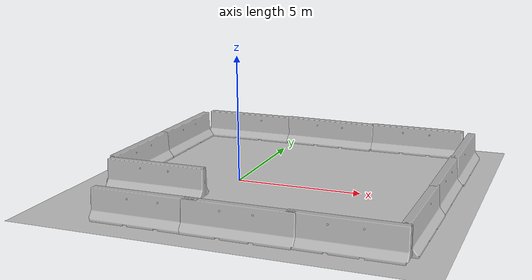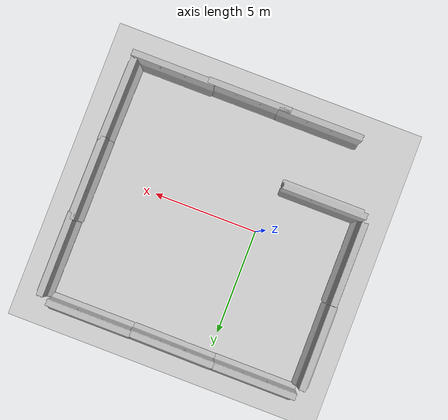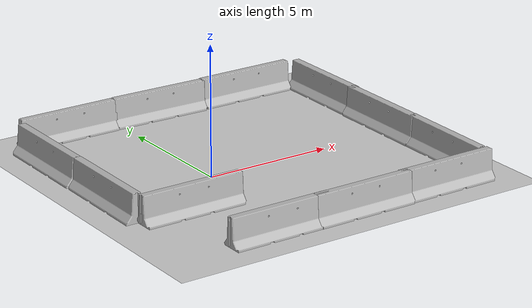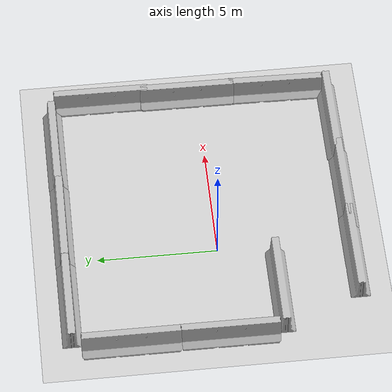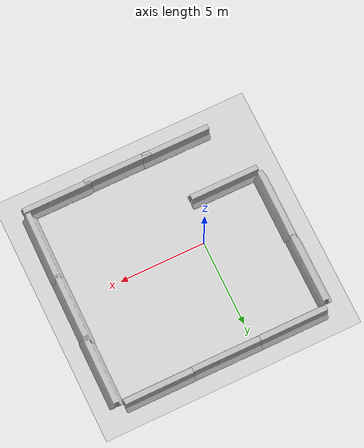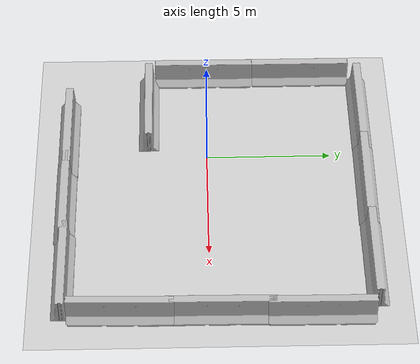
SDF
<sdf version="1.6">
 <world name="default">
  <light name="sun" type="directional">
   <pose>0 0 10 0 -0 0</pose>
   <diffuse>0.8 0.8 0.8 1</diffuse>
   <specular>0.1 0.1 0.1 1</specular>
   <attenuation>
    <range>1000</range>
    <constant>0.9</constant>
    <linear>0.01</linear>
    <quadratic>0.001</quadratic>
   </attenuation>
   <direction>-0.5 0.5 -1</direction>
  </light>
  <model name="ground_plane">
   <static>1</static>
   <link name="link">
    <collision name="collision">
     <geometry><plane><normal>0 0 1</normal><size>100 100</size></plane></geometry>
     <surface><friction><ode><mu>100</mu><mu2>50</mu2></ode></friction></surface>
    </collision>
    <visual name="visual">
     <cast_shadows>0</cast_shadows>
     <geometry><plane><normal>0 0 1</normal><size>100 100</size></plane></geometry>
     <material>
      <script><uri>file://media/materials/scripts/gazebo.material</uri><name>Gazebo/Grey</name></script>
     </material>
    </visual>
   </link>
  </model>
  <gravity>0 0 -9.8</gravity>
  <magnetic_field>6e-06 2.3e-05 -4.2e-05</magnetic_field>
  <atmosphere type="adiabatic"/>
  <physics name="default_physics" default="0" type="ode">
   <max_step_size>0.001</max_step_size>
   <real_time_factor>1</real_time_factor>
   <real_time_update_rate>1000</real_time_update_rate>
  </physics>
  <scene><ambient>0.4 0.4 0.4 1</ambient><background>0.7 0.7 0.7 1</background><shadows>1</shadows></scene>
  <spherical_coordinates>
   <surface_model>EARTH_WGS84</surface_model>
   <latitude_deg>0</latitude_deg>
   <longitude_deg>0</longitude_deg>
   <elevation>0</elevation>
   <heading_deg>0</heading_deg>
  </spherical_coordinates>
  <model name="jersey_barrier_1">
   <link name="link">
    <inertial>
     <mass>1</mass>
     <inertia><ixx>1</ixx><ixy>0</ixy><ixz>0</ixz><iyy>1</iyy><iyz>0</iyz><izz>1</izz></inertia>
    </inertial>
    <visual name="visual">
     <geometry>
      <mesh><uri>model://jersey_barrier/meshes/jersey_barrier.dae</uri><scale>1 1 1</scale></mesh>
     </geometry>
     <material><shader type="vertex"><normal_map>__default__</normal_map></shader></material>
    </visual>
    <collision name="base">
     <pose>0 0 0.032258 0 -0 0</pose>
     <geometry><box><size>4.06542 0.8107 0.064516</size></box></geometry>
     <surface>
      <friction>
       <ode><mu>1</mu><mu2>1</mu2><fdir1>0 0 0</fdir1><slip1>0</slip1><slip2>0</slip2></ode>
       <torsional>
        <coefficient>1</coefficient>
        <patch_radius>0</patch_radius>
        <surface_radius>0</surface_radius>
        <use_patch_radius>1</use_patch_radius>
        <ode><slip>0</slip></ode>
       </torsional>
      </friction>
      <bounce><restitution_coefficient>0</restitution_coefficient><threshold>1e+06</threshold></bounce>
      <contact>
       <collide_without_contact>0</collide_without_contact>
       <collide_without_contact_bitmask>1</collide_without_contact_bitmask>
       <collide_bitmask>1</collide_bitmask>
       <ode>
        <soft_cfm>0</soft_cfm>
        <soft_erp>0.2</soft_erp>
        <kp>1e+13</kp>
        <kd>1</kd>
        <max_vel>0.01</max_vel>
        <min_depth>0</min_depth>
       </ode>
       <bullet>
        <split_impulse>1</split_impulse>
        <split_impulse_penetration_threshold>-0.01</split_impulse_penetration_threshold>
        <soft_cfm>0</soft_cfm>
        <soft_erp>0.2</soft_erp>
        <kp>1e+13</kp>
        <kd>1</kd>
       </bullet>
      </contact>
     </surface>
    </collision>
    <collision name="upright">
     <pose>0 0 0.5715 0 -0 0</pose>
     <geometry><box><size>4.06542 0.3063 1.143</size></box></geometry>
     <surface>
      <friction>
       <ode><mu>1</mu><mu2>1</mu2><fdir1>0 0 0</fdir1><slip1>0</slip1><slip2>0</slip2></ode>
       <torsional>
        <coefficient>1</coefficient>
        <patch_radius>0</patch_radius>
        <surface_radius>0</surface_radius>
        <use_patch_radius>1</use_patch_radius>
        <ode><slip>0</slip></ode>
       </torsional>
      </friction>
      <bounce><restitution_coefficient>0</restitution_coefficient><threshold>1e+06</threshold></bounce>
      <contact>
       <collide_without_contact>0</collide_without_contact>
       <collide_without_contact_bitmask>1</collide_without_contact_bitmask>
       <collide_bitmask>1</collide_bitmask>
       <ode>
        <soft_cfm>0</soft_cfm>
        <soft_erp>0.2</soft_erp>
        <kp>1e+13</kp>
        <kd>1</kd>
        <max_vel>0.01</max_vel>
        <min_depth>0</min_depth>
       </ode>
       <bullet>
        <split_impulse>1</split_impulse>
        <split_impulse_penetration_threshold>-0.01</split_impulse_penetration_threshold>
        <soft_cfm>0</soft_cfm>
        <soft_erp>0.2</soft_erp>
        <kp>1e+13</kp>
        <kd>1</kd>
       </bullet>
      </contact>
     </surface>
    </collision>
    <collision name="left-angle">
     <pose>0 -0.224 0.2401 0.9 -0 0</pose>
     <geometry><box><size>4.06542 0.5 0.064516</size></box></geometry>
     <surface>
      <friction>
       <ode><mu>1</mu><mu2>1</mu2><fdir1>0 0 0</fdir1><slip1>0</slip1><slip2>0</slip2></ode>
       <torsional>
        <coefficient>1</coefficient>
        <patch_radius>0</patch_radius>
        <surface_radius>0</surface_radius>
        <use_patch_radius>1</use_patch_radius>
        <ode><slip>0</slip></ode>
       </torsional>
      </friction>
      <bounce><restitution_coefficient>0</restitution_coefficient><threshold>1e+06</threshold></bounce>
      <contact>
       <collide_without_contact>0</collide_without_contact>
       <collide_without_contact_bitmask>1</collide_without_contact_bitmask>
       <collide_bitmask>1</collide_bitmask>
       <ode>
        <soft_cfm>0</soft_cfm>
        <soft_erp>0.2</soft_erp>
        <kp>1e+13</kp>
        <kd>1</kd>
        <max_vel>0.01</max_vel>
        <min_depth>0</min_depth>
       </ode>
       <bullet>
        <split_impulse>1</split_impulse>
        <split_impulse_penetration_threshold>-0.01</split_impulse_penetration_threshold>
        <soft_cfm>0</soft_cfm>
        <soft_erp>0.2</soft_erp>
        <kp>1e+13</kp>
        <kd>1</kd>
       </bullet>
      </contact>
     </surface>
    </collision>
    <collision name="base2">
     <pose>0 0 0.1 0 -0 0</pose>
     <geometry><box><size>4.06542 0.65 0.1</size></box></geometry>
     <surface>
      <friction>
       <ode><mu>1</mu><mu2>1</mu2><fdir1>0 0 0</fdir1><slip1>0</slip1><slip2>0</slip2></ode>
       <torsional>
        <coefficient>1</coefficient>
        <patch_radius>0</patch_radius>
        <surface_radius>0</surface_radius>
        <use_patch_radius>1</use_patch_radius>
        <ode><slip>0</slip></ode>
       </torsional>
      </friction>
      <bounce><restitution_coefficient>0</restitution_coefficient><threshold>1e+06</threshold></bounce>
      <contact>
       <collide_without_contact>0</collide_without_contact>
       <collide_without_contact_bitmask>1</collide_without_contact_bitmask>
       <collide_bitmask>1</collide_bitmask>
       <ode>
        <soft_cfm>0</soft_cfm>
        <soft_erp>0.2</soft_erp>
        <kp>1e+13</kp>
        <kd>1</kd>
        <max_vel>0.01</max_vel>
        <min_depth>0</min_depth>
       </ode>
       <bullet>
        <split_impulse>1</split_impulse>
        <split_impulse_penetration_threshold>-0.01</split_impulse_penetration_threshold>
        <soft_cfm>0</soft_cfm>
        <soft_erp>0.2</soft_erp>
        <kp>1e+13</kp>
        <kd>1</kd>
       </bullet>
      </contact>
     </surface>
    </collision>
    <collision name="base3">
     <pose>0 0 0.2 0 -0 0</pose>
     <geometry><box><size>4.06542 0.5 0.1</size></box></geometry>
     <surface>
      <friction>
       <ode><mu>1</mu><mu2>1</mu2><fdir1>0 0 0</fdir1><slip1>0</slip1><slip2>0</slip2></ode>
       <torsional>
        <coefficient>1</coefficient>
        <patch_radius>0</patch_radius>
        <surface_radius>0</surface_radius>
        <use_patch_radius>1</use_patch_radius>
        <ode><slip>0</slip></ode>
       </torsional>
      </friction>
      <bounce><restitution_coefficient>0</restitution_coefficient><threshold>1e+06</threshold></bounce>
      <contact>
       <collide_without_contact>0</collide_without_contact>
       <collide_without_contact_bitmask>1</collide_without_contact_bitmask>
       <collide_bitmask>1</collide_bitmask>
       <ode>
        <soft_cfm>0</soft_cfm>
        <soft_erp>0.2</soft_erp>
        <kp>1e+13</kp>
        <kd>1</kd>
        <max_vel>0.01</max_vel>
        <min_depth>0</min_depth>
       </ode>
       <bullet>
        <split_impulse>1</split_impulse>
        <split_impulse_penetration_threshold>-0.01</split_impulse_penetration_threshold>
        <soft_cfm>0</soft_cfm>
        <soft_erp>0.2</soft_erp>
        <kp>1e+13</kp>
        <kd>1</kd>
       </bullet>
      </contact>
     </surface>
    </collision>
    <collision name="right-angle">
     <pose>0 0.224 0.2401 -0.9 0 0</pose>
     <geometry><box><size>4.06542 0.5 0.064516</size></box></geometry>
     <surface>
      <friction>
       <ode><mu>1</mu><mu2>1</mu2><fdir1>0 0 0</fdir1><slip1>0</slip1><slip2>0</slip2></ode>
       <torsional>
        <coefficient>1</coefficient>
        <patch_radius>0</patch_radius>
        <surface_radius>0</surface_radius>
        <use_patch_radius>1</use_patch_radius>
        <ode><slip>0</slip></ode>
       </torsional>
      </friction>
      <bounce><restitution_coefficient>0</restitution_coefficient><threshold>1e+06</threshold></bounce>
      <contact>
       <collide_without_contact>0</collide_without_contact>
       <collide_without_contact_bitmask>1</collide_without_contact_bitmask>
       <collide_bitmask>1</collide_bitmask>
       <ode>
        <soft_cfm>0</soft_cfm>
        <soft_erp>0.2</soft_erp>
        <kp>1e+13</kp>
        <kd>1</kd>
        <max_vel>0.01</max_vel>
        <min_depth>0</min_depth>
       </ode>
       <bullet>
        <split_impulse>1</split_impulse>
        <split_impulse_penetration_threshold>-0.01</split_impulse_penetration_threshold>
        <soft_cfm>0</soft_cfm>
        <soft_erp>0.2</soft_erp>
        <kp>1e+13</kp>
        <kd>1</kd>
       </bullet>
      </contact>
     </surface>
    </collision>
   </link>
   <static>1</static>
   <pose>-4.42746 3.95526 0 0.035823 3.4e-05 1.56986</pose>
  </model>
  <model name="jersey_barrier_0_clone_2_0_0_clone_0_clone_clone_clone">
   <link name="link">
    <inertial>
     <mass>1</mass>
     <inertia><ixx>1</ixx><ixy>0</ixy><ixz>0</ixz><iyy>1</iyy><iyz>0</iyz><izz>1</izz></inertia>
    </inertial>
    <visual name="visual">
     <geometry>
      <mesh><uri>model://jersey_barrier/meshes/jersey_barrier.dae</uri><scale>1 1 1</scale></mesh>
     </geometry>
     <material><shader type="vertex"><normal_map>__default__</normal_map></shader></material>
    </visual>
    <collision name="upright">
     <pose>0 0 0.5715 0 -0 0</pose>
     <geometry><box><size>4.06542 0.3063 1.143</size></box></geometry>
     <surface>
      <friction>
       <ode><mu>1</mu><mu2>1</mu2><fdir1>0 0 0</fdir1><slip1>0</slip1><slip2>0</slip2></ode>
       <torsional>
        <coefficient>1</coefficient>
        <patch_radius>0</patch_radius>
        <surface_radius>0</surface_radius>
        <use_patch_radius>1</use_patch_radius>
        <ode><slip>0</slip></ode>
       </torsional>
      </friction>
      <bounce><restitution_coefficient>0</restitution_coefficient><threshold>1e+06</threshold></bounce>
      <contact>
       <collide_without_contact>0</collide_without_contact>
       <collide_without_contact_bitmask>1</collide_without_contact_bitmask>
       <collide_bitmask>1</collide_bitmask>
       <ode>
        <soft_cfm>0</soft_cfm>
        <soft_erp>0.2</soft_erp>
        <kp>1e+13</kp>
        <kd>1</kd>
        <max_vel>0.01</max_vel>
        <min_depth>0</min_depth>
       </ode>
       <bullet>
        <split_impulse>1</split_impulse>
        <split_impulse_penetration_threshold>-0.01</split_impulse_penetration_threshold>
        <soft_cfm>0</soft_cfm>
        <soft_erp>0.2</soft_erp>
        <kp>1e+13</kp>
        <kd>1</kd>
       </bullet>
      </contact>
     </surface>
    </collision>
    <collision name="base3">
     <pose>0 0 0.2 0 -0 0</pose>
     <geometry><box><size>4.06542 0.5 0.1</size></box></geometry>
     <surface>
      <friction>
       <ode><mu>1</mu><mu2>1</mu2><fdir1>0 0 0</fdir1><slip1>0</slip1><slip2>0</slip2></ode>
       <torsional>
        <coefficient>1</coefficient>
        <patch_radius>0</patch_radius>
        <surface_radius>0</surface_radius>
        <use_patch_radius>1</use_patch_radius>
        <ode><slip>0</slip></ode>
       </torsional>
      </friction>
      <bounce><restitution_coefficient>0</restitution_coefficient><threshold>1e+06</threshold></bounce>
      <contact>
       <collide_without_contact>0</collide_without_contact>
       <collide_without_contact_bitmask>1</collide_without_contact_bitmask>
       <collide_bitmask>1</collide_bitmask>
       <ode>
        <soft_cfm>0</soft_cfm>
        <soft_erp>0.2</soft_erp>
        <kp>1e+13</kp>
        <kd>1</kd>
        <max_vel>0.01</max_vel>
        <min_depth>0</min_depth>
       </ode>
       <bullet>
        <split_impulse>1</split_impulse>
        <split_impulse_penetration_threshold>-0.01</split_impulse_penetration_threshold>
        <soft_cfm>0</soft_cfm>
        <soft_erp>0.2</soft_erp>
        <kp>1e+13</kp>
        <kd>1</kd>
       </bullet>
      </contact>
     </surface>
    </collision>
    <collision name="left-angle">
     <pose>0 -0.224 0.2401 0.9 -0 0</pose>
     <geometry><box><size>4.06542 0.5 0.064516</size></box></geometry>
     <surface>
      <friction>
       <ode><mu>1</mu><mu2>1</mu2><fdir1>0 0 0</fdir1><slip1>0</slip1><slip2>0</slip2></ode>
       <torsional>
        <coefficient>1</coefficient>
        <patch_radius>0</patch_radius>
        <surface_radius>0</surface_radius>
        <use_patch_radius>1</use_patch_radius>
        <ode><slip>0</slip></ode>
       </torsional>
      </friction>
      <bounce><restitution_coefficient>0</restitution_coefficient><threshold>1e+06</threshold></bounce>
      <contact>
       <collide_without_contact>0</collide_without_contact>
       <collide_without_contact_bitmask>1</collide_without_contact_bitmask>
       <collide_bitmask>1</collide_bitmask>
       <ode>
        <soft_cfm>0</soft_cfm>
        <soft_erp>0.2</soft_erp>
        <kp>1e+13</kp>
        <kd>1</kd>
        <max_vel>0.01</max_vel>
        <min_depth>0</min_depth>
       </ode>
       <bullet>
        <split_impulse>1</split_impulse>
        <split_impulse_penetration_threshold>-0.01</split_impulse_penetration_threshold>
        <soft_cfm>0</soft_cfm>
        <soft_erp>0.2</soft_erp>
        <kp>1e+13</kp>
        <kd>1</kd>
       </bullet>
      </contact>
     </surface>
    </collision>
    <collision name="base">
     <pose>0 0 0.032258 0 -0 0</pose>
     <geometry><box><size>4.06542 0.8107 0.064516</size></box></geometry>
     <surface>
      <friction>
       <ode><mu>1</mu><mu2>1</mu2><fdir1>0 0 0</fdir1><slip1>0</slip1><slip2>0</slip2></ode>
       <torsional>
        <coefficient>1</coefficient>
        <patch_radius>0</patch_radius>
        <surface_radius>0</surface_radius>
        <use_patch_radius>1</use_patch_radius>
        <ode><slip>0</slip></ode>
       </torsional>
      </friction>
      <bounce><restitution_coefficient>0</restitution_coefficient><threshold>1e+06</threshold></bounce>
      <contact>
       <collide_without_contact>0</collide_without_contact>
       <collide_without_contact_bitmask>1</collide_without_contact_bitmask>
       <collide_bitmask>1</collide_bitmask>
       <ode>
        <soft_cfm>0</soft_cfm>
        <soft_erp>0.2</soft_erp>
        <kp>1e+13</kp>
        <kd>1</kd>
        <max_vel>0.01</max_vel>
        <min_depth>0</min_depth>
       </ode>
       <bullet>
        <split_impulse>1</split_impulse>
        <split_impulse_penetration_threshold>-0.01</split_impulse_penetration_threshold>
        <soft_cfm>0</soft_cfm>
        <soft_erp>0.2</soft_erp>
        <kp>1e+13</kp>
        <kd>1</kd>
       </bullet>
      </contact>
     </surface>
    </collision>
    <collision name="base2">
     <pose>0 0 0.1 0 -0 0</pose>
     <geometry><box><size>4.06542 0.65 0.1</size></box></geometry>
     <surface>
      <friction>
       <ode><mu>1</mu><mu2>1</mu2><fdir1>0 0 0</fdir1><slip1>0</slip1><slip2>0</slip2></ode>
       <torsional>
        <coefficient>1</coefficient>
        <patch_radius>0</patch_radius>
        <surface_radius>0</surface_radius>
        <use_patch_radius>1</use_patch_radius>
        <ode><slip>0</slip></ode>
       </torsional>
      </friction>
      <bounce><restitution_coefficient>0</restitution_coefficient><threshold>1e+06</threshold></bounce>
      <contact>
       <collide_without_contact>0</collide_without_contact>
       <collide_without_contact_bitmask>1</collide_without_contact_bitmask>
       <collide_bitmask>1</collide_bitmask>
       <ode>
        <soft_cfm>0</soft_cfm>
        <soft_erp>0.2</soft_erp>
        <kp>1e+13</kp>
        <kd>1</kd>
        <max_vel>0.01</max_vel>
        <min_depth>0</min_depth>
       </ode>
       <bullet>
        <split_impulse>1</split_impulse>
        <split_impulse_penetration_threshold>-0.01</split_impulse_penetration_threshold>
        <soft_cfm>0</soft_cfm>
        <soft_erp>0.2</soft_erp>
        <kp>1e+13</kp>
        <kd>1</kd>
       </bullet>
      </contact>
     </surface>
    </collision>
    <collision name="right-angle">
     <pose>0 0.224 0.2401 -0.9 0 0</pose>
     <geometry><box><size>4.06542 0.5 0.064516</size></box></geometry>
     <surface>
      <friction>
       <ode><mu>1</mu><mu2>1</mu2><fdir1>0 0 0</fdir1><slip1>0</slip1><slip2>0</slip2></ode>
       <torsional>
        <coefficient>1</coefficient>
        <patch_radius>0</patch_radius>
        <surface_radius>0</surface_radius>
        <use_patch_radius>1</use_patch_radius>
        <ode><slip>0</slip></ode>
       </torsional>
      </friction>
      <bounce><restitution_coefficient>0</restitution_coefficient><threshold>1e+06</threshold></bounce>
      <contact>
       <collide_without_contact>0</collide_without_contact>
       <collide_without_contact_bitmask>1</collide_without_contact_bitmask>
       <collide_bitmask>1</collide_bitmask>
       <ode>
        <soft_cfm>0</soft_cfm>
        <soft_erp>0.2</soft_erp>
        <kp>1e+13</kp>
        <kd>1</kd>
        <max_vel>0.01</max_vel>
        <min_depth>0</min_depth>
       </ode>
       <bullet>
        <split_impulse>1</split_impulse>
        <split_impulse_penetration_threshold>-0.01</split_impulse_penetration_threshold>
        <soft_cfm>0</soft_cfm>
        <soft_erp>0.2</soft_erp>
        <kp>1e+13</kp>
        <kd>1</kd>
       </bullet>
      </contact>
     </surface>
    </collision>
   </link>
   <static>1</static>
   <pose>-4.39641 -0.076444 0 0 -0 1.56566</pose>
  </model>
  <model name="jersey_barrier_1_clone">
   <link name="link">
    <inertial>
     <mass>1</mass>
     <inertia><ixx>1</ixx><ixy>0</ixy><ixz>0</ixz><iyy>1</iyy><iyz>0</iyz><izz>1</izz></inertia>
    </inertial>
    <visual name="visual">
     <geometry>
      <mesh><uri>model://jersey_barrier/meshes/jersey_barrier.dae</uri><scale>1 1 1</scale></mesh>
     </geometry>
     <material><shader type="vertex"><normal_map>__default__</normal_map></shader></material>
    </visual>
    <collision name="base">
     <pose>0 0 0.032258 0 -0 0</pose>
     <geometry><box><size>4.06542 0.8107 0.064516</size></box></geometry>
     <surface>
      <friction>
       <ode><mu>1</mu><mu2>1</mu2><fdir1>0 0 0</fdir1><slip1>0</slip1><slip2>0</slip2></ode>
       <torsional>
        <coefficient>1</coefficient>
        <patch_radius>0</patch_radius>
        <surface_radius>0</surface_radius>
        <use_patch_radius>1</use_patch_radius>
        <ode><slip>0</slip></ode>
       </torsional>
      </friction>
      <bounce><restitution_coefficient>0</restitution_coefficient><threshold>1e+06</threshold></bounce>
      <contact>
       <collide_without_contact>0</collide_without_contact>
       <collide_without_contact_bitmask>1</collide_without_contact_bitmask>
       <collide_bitmask>1</collide_bitmask>
       <ode>
        <soft_cfm>0</soft_cfm>
        <soft_erp>0.2</soft_erp>
        <kp>1e+13</kp>
        <kd>1</kd>
        <max_vel>0.01</max_vel>
        <min_depth>0</min_depth>
       </ode>
       <bullet>
        <split_impulse>1</split_impulse>
        <split_impulse_penetration_threshold>-0.01</split_impulse_penetration_threshold>
        <soft_cfm>0</soft_cfm>
        <soft_erp>0.2</soft_erp>
        <kp>1e+13</kp>
        <kd>1</kd>
       </bullet>
      </contact>
     </surface>
    </collision>
    <collision name="upright">
     <pose>0 0 0.5715 0 -0 0</pose>
     <geometry><box><size>4.06542 0.3063 1.143</size></box></geometry>
     <surface>
      <friction>
       <ode><mu>1</mu><mu2>1</mu2><fdir1>0 0 0</fdir1><slip1>0</slip1><slip2>0</slip2></ode>
       <torsional>
        <coefficient>1</coefficient>
        <patch_radius>0</patch_radius>
        <surface_radius>0</surface_radius>
        <use_patch_radius>1</use_patch_radius>
        <ode><slip>0</slip></ode>
       </torsional>
      </friction>
      <bounce><restitution_coefficient>0</restitution_coefficient><threshold>1e+06</threshold></bounce>
      <contact>
       <collide_without_contact>0</collide_without_contact>
       <collide_without_contact_bitmask>1</collide_without_contact_bitmask>
       <collide_bitmask>1</collide_bitmask>
       <ode>
        <soft_cfm>0</soft_cfm>
        <soft_erp>0.2</soft_erp>
        <kp>1e+13</kp>
        <kd>1</kd>
        <max_vel>0.01</max_vel>
        <min_depth>0</min_depth>
       </ode>
       <bullet>
        <split_impulse>1</split_impulse>
        <split_impulse_penetration_threshold>-0.01</split_impulse_penetration_threshold>
        <soft_cfm>0</soft_cfm>
        <soft_erp>0.2</soft_erp>
        <kp>1e+13</kp>
        <kd>1</kd>
       </bullet>
      </contact>
     </surface>
    </collision>
    <collision name="left-angle">
     <pose>0 -0.224 0.2401 0.9 -0 0</pose>
     <geometry><box><size>4.06542 0.5 0.064516</size></box></geometry>
     <surface>
      <friction>
       <ode><mu>1</mu><mu2>1</mu2><fdir1>0 0 0</fdir1><slip1>0</slip1><slip2>0</slip2></ode>
       <torsional>
        <coefficient>1</coefficient>
        <patch_radius>0</patch_radius>
        <surface_radius>0</surface_radius>
        <use_patch_radius>1</use_patch_radius>
        <ode><slip>0</slip></ode>
       </torsional>
      </friction>
      <bounce><restitution_coefficient>0</restitution_coefficient><threshold>1e+06</threshold></bounce>
      <contact>
       <collide_without_contact>0</collide_without_contact>
       <collide_without_contact_bitmask>1</collide_without_contact_bitmask>
       <collide_bitmask>1</collide_bitmask>
       <ode>
        <soft_cfm>0</soft_cfm>
        <soft_erp>0.2</soft_erp>
        <kp>1e+13</kp>
        <kd>1</kd>
        <max_vel>0.01</max_vel>
        <min_depth>0</min_depth>
       </ode>
       <bullet>
        <split_impulse>1</split_impulse>
        <split_impulse_penetration_threshold>-0.01</split_impulse_penetration_threshold>
        <soft_cfm>0</soft_cfm>
        <soft_erp>0.2</soft_erp>
        <kp>1e+13</kp>
        <kd>1</kd>
       </bullet>
      </contact>
     </surface>
    </collision>
    <collision name="base2">
     <pose>0 0 0.1 0 -0 0</pose>
     <geometry><box><size>4.06542 0.65 0.1</size></box></geometry>
     <surface>
      <friction>
       <ode><mu>1</mu><mu2>1</mu2><fdir1>0 0 0</fdir1><slip1>0</slip1><slip2>0</slip2></ode>
       <torsional>
        <coefficient>1</coefficient>
        <patch_radius>0</patch_radius>
        <surface_radius>0</surface_radius>
        <use_patch_radius>1</use_patch_radius>
        <ode><slip>0</slip></ode>
       </torsional>
      </friction>
      <bounce><restitution_coefficient>0</restitution_coefficient><threshold>1e+06</threshold></bounce>
      <contact>
       <collide_without_contact>0</collide_without_contact>
       <collide_without_contact_bitmask>1</collide_without_contact_bitmask>
       <collide_bitmask>1</collide_bitmask>
       <ode>
        <soft_cfm>0</soft_cfm>
        <soft_erp>0.2</soft_erp>
        <kp>1e+13</kp>
        <kd>1</kd>
        <max_vel>0.01</max_vel>
        <min_depth>0</min_depth>
       </ode>
       <bullet>
        <split_impulse>1</split_impulse>
        <split_impulse_penetration_threshold>-0.01</split_impulse_penetration_threshold>
        <soft_cfm>0</soft_cfm>
        <soft_erp>0.2</soft_erp>
        <kp>1e+13</kp>
        <kd>1</kd>
       </bullet>
      </contact>
     </surface>
    </collision>
    <collision name="base3">
     <pose>0 0 0.2 0 -0 0</pose>
     <geometry><box><size>4.06542 0.5 0.1</size></box></geometry>
     <surface>
      <friction>
       <ode><mu>1</mu><mu2>1</mu2><fdir1>0 0 0</fdir1><slip1>0</slip1><slip2>0</slip2></ode>
       <torsional>
        <coefficient>1</coefficient>
        <patch_radius>0</patch_radius>
        <surface_radius>0</surface_radius>
        <use_patch_radius>1</use_patch_radius>
        <ode><slip>0</slip></ode>
       </torsional>
      </friction>
      <bounce><restitution_coefficient>0</restitution_coefficient><threshold>1e+06</threshold></bounce>
      <contact>
       <collide_without_contact>0</collide_without_contact>
       <collide_without_contact_bitmask>1</collide_without_contact_bitmask>
       <collide_bitmask>1</collide_bitmask>
       <ode>
        <soft_cfm>0</soft_cfm>
        <soft_erp>0.2</soft_erp>
        <kp>1e+13</kp>
        <kd>1</kd>
        <max_vel>0.01</max_vel>
        <min_depth>0</min_depth>
       </ode>
       <bullet>
        <split_impulse>1</split_impulse>
        <split_impulse_penetration_threshold>-0.01</split_impulse_penetration_threshold>
        <soft_cfm>0</soft_cfm>
        <soft_erp>0.2</soft_erp>
        <kp>1e+13</kp>
        <kd>1</kd>
       </bullet>
      </contact>
     </surface>
    </collision>
    <collision name="right-angle">
     <pose>0 0.224 0.2401 -0.9 0 0</pose>
     <geometry><box><size>4.06542 0.5 0.064516</size></box></geometry>
     <surface>
      <friction>
       <ode><mu>1</mu><mu2>1</mu2><fdir1>0 0 0</fdir1><slip1>0</slip1><slip2>0</slip2></ode>
       <torsional>
        <coefficient>1</coefficient>
        <patch_radius>0</patch_radius>
        <surface_radius>0</surface_radius>
        <use_patch_radius>1</use_patch_radius>
        <ode><slip>0</slip></ode>
       </torsional>
      </friction>
      <bounce><restitution_coefficient>0</restitution_coefficient><threshold>1e+06</threshold></bounce>
      <contact>
       <collide_without_contact>0</collide_without_contact>
       <collide_without_contact_bitmask>1</collide_without_contact_bitmask>
       <collide_bitmask>1</collide_bitmask>
       <ode>
        <soft_cfm>0</soft_cfm>
        <soft_erp>0.2</soft_erp>
        <kp>1e+13</kp>
        <kd>1</kd>
        <max_vel>0.01</max_vel>
        <min_depth>0</min_depth>
       </ode>
       <bullet>
        <split_impulse>1</split_impulse>
        <split_impulse_penetration_threshold>-0.01</split_impulse_penetration_threshold>
        <soft_cfm>0</soft_cfm>
        <soft_erp>0.2</soft_erp>
        <kp>1e+13</kp>
        <kd>1</kd>
       </bullet>
      </contact>
     </surface>
    </collision>
   </link>
   <static>1</static>
   <pose>1.74259 6.33982 0 -0.010959 -0.007344 3.13544</pose>
  </model>
  <model name="jersey_barrier_0_clone_2">
   <link name="link">
    <inertial>
     <mass>1</mass>
     <inertia><ixx>1</ixx><ixy>0</ixy><ixz>0</ixz><iyy>1</iyy><iyz>0</iyz><izz>1</izz></inertia>
    </inertial>
    <visual name="visual">
     <geometry>
      <mesh><uri>model://jersey_barrier/meshes/jersey_barrier.dae</uri><scale>1 1 1</scale></mesh>
     </geometry>
     <material><shader type="vertex"><normal_map>__default__</normal_map></shader></material>
    </visual>
    <collision name="upright">
     <pose>0 0 0.5715 0 -0 0</pose>
     <geometry><box><size>4.06542 0.3063 1.143</size></box></geometry>
     <surface>
      <friction>
       <ode><mu>1</mu><mu2>1</mu2><fdir1>0 0 0</fdir1><slip1>0</slip1><slip2>0</slip2></ode>
       <torsional>
        <coefficient>1</coefficient>
        <patch_radius>0</patch_radius>
        <surface_radius>0</surface_radius>
        <use_patch_radius>1</use_patch_radius>
        <ode><slip>0</slip></ode>
       </torsional>
      </friction>
      <bounce><restitution_coefficient>0</restitution_coefficient><threshold>1e+06</threshold></bounce>
      <contact>
       <collide_without_contact>0</collide_without_contact>
       <collide_without_contact_bitmask>1</collide_without_contact_bitmask>
       <collide_bitmask>1</collide_bitmask>
       <ode>
        <soft_cfm>0</soft_cfm>
        <soft_erp>0.2</soft_erp>
        <kp>1e+13</kp>
        <kd>1</kd>
        <max_vel>0.01</max_vel>
        <min_depth>0</min_depth>
       </ode>
       <bullet>
        <split_impulse>1</split_impulse>
        <split_impulse_penetration_threshold>-0.01</split_impulse_penetration_threshold>
        <soft_cfm>0</soft_cfm>
        <soft_erp>0.2</soft_erp>
        <kp>1e+13</kp>
        <kd>1</kd>
       </bullet>
      </contact>
     </surface>
    </collision>
    <collision name="base3">
     <pose>0 0 0.2 0 -0 0</pose>
     <geometry><box><size>4.06542 0.5 0.1</size></box></geometry>
     <surface>
      <friction>
       <ode><mu>1</mu><mu2>1</mu2><fdir1>0 0 0</fdir1><slip1>0</slip1><slip2>0</slip2></ode>
       <torsional>
        <coefficient>1</coefficient>
        <patch_radius>0</patch_radius>
        <surface_radius>0</surface_radius>
        <use_patch_radius>1</use_patch_radius>
        <ode><slip>0</slip></ode>
       </torsional>
      </friction>
      <bounce><restitution_coefficient>0</restitution_coefficient><threshold>1e+06</threshold></bounce>
      <contact>
       <collide_without_contact>0</collide_without_contact>
       <collide_without_contact_bitmask>1</collide_without_contact_bitmask>
       <collide_bitmask>1</collide_bitmask>
       <ode>
        <soft_cfm>0</soft_cfm>
        <soft_erp>0.2</soft_erp>
        <kp>1e+13</kp>
        <kd>1</kd>
        <max_vel>0.01</max_vel>
        <min_depth>0</min_depth>
       </ode>
       <bullet>
        <split_impulse>1</split_impulse>
        <split_impulse_penetration_threshold>-0.01</split_impulse_penetration_threshold>
        <soft_cfm>0</soft_cfm>
        <soft_erp>0.2</soft_erp>
        <kp>1e+13</kp>
        <kd>1</kd>
       </bullet>
      </contact>
     </surface>
    </collision>
    <collision name="base">
     <pose>0 0 0.032258 0 -0 0</pose>
     <geometry><box><size>4.06542 0.8107 0.064516</size></box></geometry>
     <surface>
      <friction>
       <ode><mu>1</mu><mu2>1</mu2><fdir1>0 0 0</fdir1><slip1>0</slip1><slip2>0</slip2></ode>
       <torsional>
        <coefficient>1</coefficient>
        <patch_radius>0</patch_radius>
        <surface_radius>0</surface_radius>
        <use_patch_radius>1</use_patch_radius>
        <ode><slip>0</slip></ode>
       </torsional>
      </friction>
      <bounce><restitution_coefficient>0</restitution_coefficient><threshold>1e+06</threshold></bounce>
      <contact>
       <collide_without_contact>0</collide_without_contact>
       <collide_without_contact_bitmask>1</collide_without_contact_bitmask>
       <collide_bitmask>1</collide_bitmask>
       <ode>
        <soft_cfm>0</soft_cfm>
        <soft_erp>0.2</soft_erp>
        <kp>1e+13</kp>
        <kd>1</kd>
        <max_vel>0.01</max_vel>
        <min_depth>0</min_depth>
       </ode>
       <bullet>
        <split_impulse>1</split_impulse>
        <split_impulse_penetration_threshold>-0.01</split_impulse_penetration_threshold>
        <soft_cfm>0</soft_cfm>
        <soft_erp>0.2</soft_erp>
        <kp>1e+13</kp>
        <kd>1</kd>
       </bullet>
      </contact>
     </surface>
    </collision>
    <collision name="base2">
     <pose>0 0 0.1 0 -0 0</pose>
     <geometry><box><size>4.06542 0.65 0.1</size></box></geometry>
     <surface>
      <friction>
       <ode><mu>1</mu><mu2>1</mu2><fdir1>0 0 0</fdir1><slip1>0</slip1><slip2>0</slip2></ode>
       <torsional>
        <coefficient>1</coefficient>
        <patch_radius>0</patch_radius>
        <surface_radius>0</surface_radius>
        <use_patch_radius>1</use_patch_radius>
        <ode><slip>0</slip></ode>
       </torsional>
      </friction>
      <bounce><restitution_coefficient>0</restitution_coefficient><threshold>1e+06</threshold></bounce>
      <contact>
       <collide_without_contact>0</collide_without_contact>
       <collide_without_contact_bitmask>1</collide_without_contact_bitmask>
       <collide_bitmask>1</collide_bitmask>
       <ode>
        <soft_cfm>0</soft_cfm>
        <soft_erp>0.2</soft_erp>
        <kp>1e+13</kp>
        <kd>1</kd>
        <max_vel>0.01</max_vel>
        <min_depth>0</min_depth>
       </ode>
       <bullet>
        <split_impulse>1</split_impulse>
        <split_impulse_penetration_threshold>-0.01</split_impulse_penetration_threshold>
        <soft_cfm>0</soft_cfm>
        <soft_erp>0.2</soft_erp>
        <kp>1e+13</kp>
        <kd>1</kd>
       </bullet>
      </contact>
     </surface>
    </collision>
    <collision name="left-angle">
     <pose>0 -0.224 0.2401 0.9 -0 0</pose>
     <geometry><box><size>4.06542 0.5 0.064516</size></box></geometry>
     <surface>
      <friction>
       <ode><mu>1</mu><mu2>1</mu2><fdir1>0 0 0</fdir1><slip1>0</slip1><slip2>0</slip2></ode>
       <torsional>
        <coefficient>1</coefficient>
        <patch_radius>0</patch_radius>
        <surface_radius>0</surface_radius>
        <use_patch_radius>1</use_patch_radius>
        <ode><slip>0</slip></ode>
       </torsional>
      </friction>
      <bounce><restitution_coefficient>0</restitution_coefficient><threshold>1e+06</threshold></bounce>
      <contact>
       <collide_without_contact>0</collide_without_contact>
       <collide_without_contact_bitmask>1</collide_without_contact_bitmask>
       <collide_bitmask>1</collide_bitmask>
       <ode>
        <soft_cfm>0</soft_cfm>
        <soft_erp>0.2</soft_erp>
        <kp>1e+13</kp>
        <kd>1</kd>
        <max_vel>0.01</max_vel>
        <min_depth>0</min_depth>
       </ode>
       <bullet>
        <split_impulse>1</split_impulse>
        <split_impulse_penetration_threshold>-0.01</split_impulse_penetration_threshold>
        <soft_cfm>0</soft_cfm>
        <soft_erp>0.2</soft_erp>
        <kp>1e+13</kp>
        <kd>1</kd>
       </bullet>
      </contact>
     </surface>
    </collision>
    <collision name="right-angle">
     <pose>0 0.224 0.2401 -0.9 0 0</pose>
     <geometry><box><size>4.06542 0.5 0.064516</size></box></geometry>
     <surface>
      <friction>
       <ode><mu>1</mu><mu2>1</mu2><fdir1>0 0 0</fdir1><slip1>0</slip1><slip2>0</slip2></ode>
       <torsional>
        <coefficient>1</coefficient>
        <patch_radius>0</patch_radius>
        <surface_radius>0</surface_radius>
        <use_patch_radius>1</use_patch_radius>
        <ode><slip>0</slip></ode>
       </torsional>
      </friction>
      <bounce><restitution_coefficient>0</restitution_coefficient><threshold>1e+06</threshold></bounce>
      <contact>
       <collide_without_contact>0</collide_without_contact>
       <collide_without_contact_bitmask>1</collide_without_contact_bitmask>
       <collide_bitmask>1</collide_bitmask>
       <ode>
        <soft_cfm>0</soft_cfm>
        <soft_erp>0.2</soft_erp>
        <kp>1e+13</kp>
        <kd>1</kd>
        <max_vel>0.01</max_vel>
        <min_depth>0</min_depth>
       </ode>
       <bullet>
        <split_impulse>1</split_impulse>
        <split_impulse_penetration_threshold>-0.01</split_impulse_penetration_threshold>
        <soft_cfm>0</soft_cfm>
        <soft_erp>0.2</soft_erp>
        <kp>1e+13</kp>
        <kd>1</kd>
       </bullet>
      </contact>
     </surface>
    </collision>
   </link>
   <static>1</static>
   <pose>-2.37045 -2.36278 0 0 -0 0</pose>
  </model>
  <model name="jersey_barrier_0_clone_2_1">
   <link name="link">
    <inertial>
     <mass>1</mass>
     <inertia><ixx>1</ixx><ixy>0</ixy><ixz>0</ixz><iyy>1</iyy><iyz>0</iyz><izz>1</izz></inertia>
    </inertial>
    <visual name="visual">
     <geometry>
      <mesh><uri>model://jersey_barrier/meshes/jersey_barrier.dae</uri><scale>1 1 1</scale></mesh>
     </geometry>
     <material><shader type="vertex"><normal_map>__default__</normal_map></shader></material>
    </visual>
    <collision name="upright">
     <pose>0 0 0.5715 0 -0 0</pose>
     <geometry><box><size>4.06542 0.3063 1.143</size></box></geometry>
     <surface>
      <friction>
       <ode><mu>1</mu><mu2>1</mu2><fdir1>0 0 0</fdir1><slip1>0</slip1><slip2>0</slip2></ode>
       <torsional>
        <coefficient>1</coefficient>
        <patch_radius>0</patch_radius>
        <surface_radius>0</surface_radius>
        <use_patch_radius>1</use_patch_radius>
        <ode><slip>0</slip></ode>
       </torsional>
      </friction>
      <bounce><restitution_coefficient>0</restitution_coefficient><threshold>1e+06</threshold></bounce>
      <contact>
       <collide_without_contact>0</collide_without_contact>
       <collide_without_contact_bitmask>1</collide_without_contact_bitmask>
       <collide_bitmask>1</collide_bitmask>
       <ode>
        <soft_cfm>0</soft_cfm>
        <soft_erp>0.2</soft_erp>
        <kp>1e+13</kp>
        <kd>1</kd>
        <max_vel>0.01</max_vel>
        <min_depth>0</min_depth>
       </ode>
       <bullet>
        <split_impulse>1</split_impulse>
        <split_impulse_penetration_threshold>-0.01</split_impulse_penetration_threshold>
        <soft_cfm>0</soft_cfm>
        <soft_erp>0.2</soft_erp>
        <kp>1e+13</kp>
        <kd>1</kd>
       </bullet>
      </contact>
     </surface>
    </collision>
    <collision name="base3">
     <pose>0 0 0.2 0 -0 0</pose>
     <geometry><box><size>4.06542 0.5 0.1</size></box></geometry>
     <surface>
      <friction>
       <ode><mu>1</mu><mu2>1</mu2><fdir1>0 0 0</fdir1><slip1>0</slip1><slip2>0</slip2></ode>
       <torsional>
        <coefficient>1</coefficient>
        <patch_radius>0</patch_radius>
        <surface_radius>0</surface_radius>
        <use_patch_radius>1</use_patch_radius>
        <ode><slip>0</slip></ode>
       </torsional>
      </friction>
      <bounce><restitution_coefficient>0</restitution_coefficient><threshold>1e+06</threshold></bounce>
      <contact>
       <collide_without_contact>0</collide_without_contact>
       <collide_without_contact_bitmask>1</collide_without_contact_bitmask>
       <collide_bitmask>1</collide_bitmask>
       <ode>
        <soft_cfm>0</soft_cfm>
        <soft_erp>0.2</soft_erp>
        <kp>1e+13</kp>
        <kd>1</kd>
        <max_vel>0.01</max_vel>
        <min_depth>0</min_depth>
       </ode>
       <bullet>
        <split_impulse>1</split_impulse>
        <split_impulse_penetration_threshold>-0.01</split_impulse_penetration_threshold>
        <soft_cfm>0</soft_cfm>
        <soft_erp>0.2</soft_erp>
        <kp>1e+13</kp>
        <kd>1</kd>
       </bullet>
      </contact>
     </surface>
    </collision>
    <collision name="base">
     <pose>0 0 0.032258 0 -0 0</pose>
     <geometry><box><size>4.06542 0.8107 0.064516</size></box></geometry>
     <surface>
      <friction>
       <ode><mu>1</mu><mu2>1</mu2><fdir1>0 0 0</fdir1><slip1>0</slip1><slip2>0</slip2></ode>
       <torsional>
        <coefficient>1</coefficient>
        <patch_radius>0</patch_radius>
        <surface_radius>0</surface_radius>
        <use_patch_radius>1</use_patch_radius>
        <ode><slip>0</slip></ode>
       </torsional>
      </friction>
      <bounce><restitution_coefficient>0</restitution_coefficient><threshold>1e+06</threshold></bounce>
      <contact>
       <collide_without_contact>0</collide_without_contact>
       <collide_without_contact_bitmask>1</collide_without_contact_bitmask>
       <collide_bitmask>1</collide_bitmask>
       <ode>
        <soft_cfm>0</soft_cfm>
        <soft_erp>0.2</soft_erp>
        <kp>1e+13</kp>
        <kd>1</kd>
        <max_vel>0.01</max_vel>
        <min_depth>0</min_depth>
       </ode>
       <bullet>
        <split_impulse>1</split_impulse>
        <split_impulse_penetration_threshold>-0.01</split_impulse_penetration_threshold>
        <soft_cfm>0</soft_cfm>
        <soft_erp>0.2</soft_erp>
        <kp>1e+13</kp>
        <kd>1</kd>
       </bullet>
      </contact>
     </surface>
    </collision>
    <collision name="base2">
     <pose>0 0 0.1 0 -0 0</pose>
     <geometry><box><size>4.06542 0.65 0.1</size></box></geometry>
     <surface>
      <friction>
       <ode><mu>1</mu><mu2>1</mu2><fdir1>0 0 0</fdir1><slip1>0</slip1><slip2>0</slip2></ode>
       <torsional>
        <coefficient>1</coefficient>
        <patch_radius>0</patch_radius>
        <surface_radius>0</surface_radius>
        <use_patch_radius>1</use_patch_radius>
        <ode><slip>0</slip></ode>
       </torsional>
      </friction>
      <bounce><restitution_coefficient>0</restitution_coefficient><threshold>1e+06</threshold></bounce>
      <contact>
       <collide_without_contact>0</collide_without_contact>
       <collide_without_contact_bitmask>1</collide_without_contact_bitmask>
       <collide_bitmask>1</collide_bitmask>
       <ode>
        <soft_cfm>0</soft_cfm>
        <soft_erp>0.2</soft_erp>
        <kp>1e+13</kp>
        <kd>1</kd>
        <max_vel>0.01</max_vel>
        <min_depth>0</min_depth>
       </ode>
       <bullet>
        <split_impulse>1</split_impulse>
        <split_impulse_penetration_threshold>-0.01</split_impulse_penetration_threshold>
        <soft_cfm>0</soft_cfm>
        <soft_erp>0.2</soft_erp>
        <kp>1e+13</kp>
        <kd>1</kd>
       </bullet>
      </contact>
     </surface>
    </collision>
    <collision name="left-angle">
     <pose>0 -0.224 0.2401 0.9 -0 0</pose>
     <geometry><box><size>4.06542 0.5 0.064516</size></box></geometry>
     <surface>
      <friction>
       <ode><mu>1</mu><mu2>1</mu2><fdir1>0 0 0</fdir1><slip1>0</slip1><slip2>0</slip2></ode>
       <torsional>
        <coefficient>1</coefficient>
        <patch_radius>0</patch_radius>
        <surface_radius>0</surface_radius>
        <use_patch_radius>1</use_patch_radius>
        <ode><slip>0</slip></ode>
       </torsional>
      </friction>
      <bounce><restitution_coefficient>0</restitution_coefficient><threshold>1e+06</threshold></bounce>
      <contact>
       <collide_without_contact>0</collide_without_contact>
       <collide_without_contact_bitmask>1</collide_without_contact_bitmask>
       <collide_bitmask>1</collide_bitmask>
       <ode>
        <soft_cfm>0</soft_cfm>
        <soft_erp>0.2</soft_erp>
        <kp>1e+13</kp>
        <kd>1</kd>
        <max_vel>0.01</max_vel>
        <min_depth>0</min_depth>
       </ode>
       <bullet>
        <split_impulse>1</split_impulse>
        <split_impulse_penetration_threshold>-0.01</split_impulse_penetration_threshold>
        <soft_cfm>0</soft_cfm>
        <soft_erp>0.2</soft_erp>
        <kp>1e+13</kp>
        <kd>1</kd>
       </bullet>
      </contact>
     </surface>
    </collision>
    <collision name="right-angle">
     <pose>0 0.224 0.2401 -0.9 0 0</pose>
     <geometry><box><size>4.06542 0.5 0.064516</size></box></geometry>
     <surface>
      <friction>
       <ode><mu>1</mu><mu2>1</mu2><fdir1>0 0 0</fdir1><slip1>0</slip1><slip2>0</slip2></ode>
       <torsional>
        <coefficient>1</coefficient>
        <patch_radius>0</patch_radius>
        <surface_radius>0</surface_radius>
        <use_patch_radius>1</use_patch_radius>
        <ode><slip>0</slip></ode>
       </torsional>
      </friction>
      <bounce><restitution_coefficient>0</restitution_coefficient><threshold>1e+06</threshold></bounce>
      <contact>
       <collide_without_contact>0</collide_without_contact>
       <collide_without_contact_bitmask>1</collide_without_contact_bitmask>
       <collide_bitmask>1</collide_bitmask>
       <ode>
        <soft_cfm>0</soft_cfm>
        <soft_erp>0.2</soft_erp>
        <kp>1e+13</kp>
        <kd>1</kd>
        <max_vel>0.01</max_vel>
        <min_depth>0</min_depth>
       </ode>
       <bullet>
        <split_impulse>1</split_impulse>
        <split_impulse_penetration_threshold>-0.01</split_impulse_penetration_threshold>
        <soft_cfm>0</soft_cfm>
        <soft_erp>0.2</soft_erp>
        <kp>1e+13</kp>
        <kd>1</kd>
       </bullet>
      </contact>
     </surface>
    </collision>
   </link>
   <static>1</static>
   <pose>2.50416 -5.64344 0 0 -0 0</pose>
  </model>
  <model name="jersey_barrier_0_clone_2_2">
   <link name="link">
    <inertial>
     <mass>1</mass>
     <inertia><ixx>1</ixx><ixy>0</ixy><ixz>0</ixz><iyy>1</iyy><iyz>0</iyz><izz>1</izz></inertia>
    </inertial>
    <visual name="visual">
     <geometry>
      <mesh><uri>model://jersey_barrier/meshes/jersey_barrier.dae</uri><scale>1 1 1</scale></mesh>
     </geometry>
     <material><shader type="vertex"><normal_map>__default__</normal_map></shader></material>
    </visual>
    <collision name="upright">
     <pose>0 0 0.5715 0 -0 0</pose>
     <geometry><box><size>4.06542 0.3063 1.143</size></box></geometry>
     <surface>
      <friction>
       <ode><mu>1</mu><mu2>1</mu2><fdir1>0 0 0</fdir1><slip1>0</slip1><slip2>0</slip2></ode>
       <torsional>
        <coefficient>1</coefficient>
        <patch_radius>0</patch_radius>
        <surface_radius>0</surface_radius>
        <use_patch_radius>1</use_patch_radius>
        <ode><slip>0</slip></ode>
       </torsional>
      </friction>
      <bounce><restitution_coefficient>0</restitution_coefficient><threshold>1e+06</threshold></bounce>
      <contact>
       <collide_without_contact>0</collide_without_contact>
       <collide_without_contact_bitmask>1</collide_without_contact_bitmask>
       <collide_bitmask>1</collide_bitmask>
       <ode>
        <soft_cfm>0</soft_cfm>
        <soft_erp>0.2</soft_erp>
        <kp>1e+13</kp>
        <kd>1</kd>
        <max_vel>0.01</max_vel>
        <min_depth>0</min_depth>
       </ode>
       <bullet>
        <split_impulse>1</split_impulse>
        <split_impulse_penetration_threshold>-0.01</split_impulse_penetration_threshold>
        <soft_cfm>0</soft_cfm>
        <soft_erp>0.2</soft_erp>
        <kp>1e+13</kp>
        <kd>1</kd>
       </bullet>
      </contact>
     </surface>
    </collision>
    <collision name="base3">
     <pose>0 0 0.2 0 -0 0</pose>
     <geometry><box><size>4.06542 0.5 0.1</size></box></geometry>
     <surface>
      <friction>
       <ode><mu>1</mu><mu2>1</mu2><fdir1>0 0 0</fdir1><slip1>0</slip1><slip2>0</slip2></ode>
       <torsional>
        <coefficient>1</coefficient>
        <patch_radius>0</patch_radius>
        <surface_radius>0</surface_radius>
        <use_patch_radius>1</use_patch_radius>
        <ode><slip>0</slip></ode>
       </torsional>
      </friction>
      <bounce><restitution_coefficient>0</restitution_coefficient><threshold>1e+06</threshold></bounce>
      <contact>
       <collide_without_contact>0</collide_without_contact>
       <collide_without_contact_bitmask>1</collide_without_contact_bitmask>
       <collide_bitmask>1</collide_bitmask>
       <ode>
        <soft_cfm>0</soft_cfm>
        <soft_erp>0.2</soft_erp>
        <kp>1e+13</kp>
        <kd>1</kd>
        <max_vel>0.01</max_vel>
        <min_depth>0</min_depth>
       </ode>
       <bullet>
        <split_impulse>1</split_impulse>
        <split_impulse_penetration_threshold>-0.01</split_impulse_penetration_threshold>
        <soft_cfm>0</soft_cfm>
        <soft_erp>0.2</soft_erp>
        <kp>1e+13</kp>
        <kd>1</kd>
       </bullet>
      </contact>
     </surface>
    </collision>
    <collision name="base">
     <pose>0 0 0.032258 0 -0 0</pose>
     <geometry><box><size>4.06542 0.8107 0.064516</size></box></geometry>
     <surface>
      <friction>
       <ode><mu>1</mu><mu2>1</mu2><fdir1>0 0 0</fdir1><slip1>0</slip1><slip2>0</slip2></ode>
       <torsional>
        <coefficient>1</coefficient>
        <patch_radius>0</patch_radius>
        <surface_radius>0</surface_radius>
        <use_patch_radius>1</use_patch_radius>
        <ode><slip>0</slip></ode>
       </torsional>
      </friction>
      <bounce><restitution_coefficient>0</restitution_coefficient><threshold>1e+06</threshold></bounce>
      <contact>
       <collide_without_contact>0</collide_without_contact>
       <collide_without_contact_bitmask>1</collide_without_contact_bitmask>
       <collide_bitmask>1</collide_bitmask>
       <ode>
        <soft_cfm>0</soft_cfm>
        <soft_erp>0.2</soft_erp>
        <kp>1e+13</kp>
        <kd>1</kd>
        <max_vel>0.01</max_vel>
        <min_depth>0</min_depth>
       </ode>
       <bullet>
        <split_impulse>1</split_impulse>
        <split_impulse_penetration_threshold>-0.01</split_impulse_penetration_threshold>
        <soft_cfm>0</soft_cfm>
        <soft_erp>0.2</soft_erp>
        <kp>1e+13</kp>
        <kd>1</kd>
       </bullet>
      </contact>
     </surface>
    </collision>
    <collision name="base2">
     <pose>0 0 0.1 0 -0 0</pose>
     <geometry><box><size>4.06542 0.65 0.1</size></box></geometry>
     <surface>
      <friction>
       <ode><mu>1</mu><mu2>1</mu2><fdir1>0 0 0</fdir1><slip1>0</slip1><slip2>0</slip2></ode>
       <torsional>
        <coefficient>1</coefficient>
        <patch_radius>0</patch_radius>
        <surface_radius>0</surface_radius>
        <use_patch_radius>1</use_patch_radius>
        <ode><slip>0</slip></ode>
       </torsional>
      </friction>
      <bounce><restitution_coefficient>0</restitution_coefficient><threshold>1e+06</threshold></bounce>
      <contact>
       <collide_without_contact>0</collide_without_contact>
       <collide_without_contact_bitmask>1</collide_without_contact_bitmask>
       <collide_bitmask>1</collide_bitmask>
       <ode>
        <soft_cfm>0</soft_cfm>
        <soft_erp>0.2</soft_erp>
        <kp>1e+13</kp>
        <kd>1</kd>
        <max_vel>0.01</max_vel>
        <min_depth>0</min_depth>
       </ode>
       <bullet>
        <split_impulse>1</split_impulse>
        <split_impulse_penetration_threshold>-0.01</split_impulse_penetration_threshold>
        <soft_cfm>0</soft_cfm>
        <soft_erp>0.2</soft_erp>
        <kp>1e+13</kp>
        <kd>1</kd>
       </bullet>
      </contact>
     </surface>
    </collision>
    <collision name="left-angle">
     <pose>0 -0.224 0.2401 0.9 -0 0</pose>
     <geometry><box><size>4.06542 0.5 0.064516</size></box></geometry>
     <surface>
      <friction>
       <ode><mu>1</mu><mu2>1</mu2><fdir1>0 0 0</fdir1><slip1>0</slip1><slip2>0</slip2></ode>
       <torsional>
        <coefficient>1</coefficient>
        <patch_radius>0</patch_radius>
        <surface_radius>0</surface_radius>
        <use_patch_radius>1</use_patch_radius>
        <ode><slip>0</slip></ode>
       </torsional>
      </friction>
      <bounce><restitution_coefficient>0</restitution_coefficient><threshold>1e+06</threshold></bounce>
      <contact>
       <collide_without_contact>0</collide_without_contact>
       <collide_without_contact_bitmask>1</collide_without_contact_bitmask>
       <collide_bitmask>1</collide_bitmask>
       <ode>
        <soft_cfm>0</soft_cfm>
        <soft_erp>0.2</soft_erp>
        <kp>1e+13</kp>
        <kd>1</kd>
        <max_vel>0.01</max_vel>
        <min_depth>0</min_depth>
       </ode>
       <bullet>
        <split_impulse>1</split_impulse>
        <split_impulse_penetration_threshold>-0.01</split_impulse_penetration_threshold>
        <soft_cfm>0</soft_cfm>
        <soft_erp>0.2</soft_erp>
        <kp>1e+13</kp>
        <kd>1</kd>
       </bullet>
      </contact>
     </surface>
    </collision>
    <collision name="right-angle">
     <pose>0 0.224 0.2401 -0.9 0 0</pose>
     <geometry><box><size>4.06542 0.5 0.064516</size></box></geometry>
     <surface>
      <friction>
       <ode><mu>1</mu><mu2>1</mu2><fdir1>0 0 0</fdir1><slip1>0</slip1><slip2>0</slip2></ode>
       <torsional>
        <coefficient>1</coefficient>
        <patch_radius>0</patch_radius>
        <surface_radius>0</surface_radius>
        <use_patch_radius>1</use_patch_radius>
        <ode><slip>0</slip></ode>
       </torsional>
      </friction>
      <bounce><restitution_coefficient>0</restitution_coefficient><threshold>1e+06</threshold></bounce>
      <contact>
       <collide_without_contact>0</collide_without_contact>
       <collide_without_contact_bitmask>1</collide_without_contact_bitmask>
       <collide_bitmask>1</collide_bitmask>
       <ode>
        <soft_cfm>0</soft_cfm>
        <soft_erp>0.2</soft_erp>
        <kp>1e+13</kp>
        <kd>1</kd>
        <max_vel>0.01</max_vel>
        <min_depth>0</min_depth>
       </ode>
       <bullet>
        <split_impulse>1</split_impulse>
        <split_impulse_penetration_threshold>-0.01</split_impulse_penetration_threshold>
        <soft_cfm>0</soft_cfm>
        <soft_erp>0.2</soft_erp>
        <kp>1e+13</kp>
        <kd>1</kd>
       </bullet>
      </contact>
     </surface>
    </collision>
   </link>
   <static>1</static>
   <pose>-2.21283 6.3442 0 0 -0 0</pose>
  </model>
  <model name="jersey_barrier_0_clone_2_3">
   <link name="link">
    <inertial>
     <mass>1</mass>
     <inertia><ixx>1</ixx><ixy>0</ixy><ixz>0</ixz><iyy>1</iyy><iyz>0</iyz><izz>1</izz></inertia>
    </inertial>
    <visual name="visual">
     <geometry>
      <mesh><uri>model://jersey_barrier/meshes/jersey_barrier.dae</uri><scale>1 1 1</scale></mesh>
     </geometry>
     <material><shader type="vertex"><normal_map>__default__</normal_map></shader></material>
    </visual>
    <collision name="upright">
     <pose>0 0 0.5715 0 -0 0</pose>
     <geometry><box><size>4.06542 0.3063 1.143</size></box></geometry>
     <surface>
      <friction>
       <ode><mu>1</mu><mu2>1</mu2><fdir1>0 0 0</fdir1><slip1>0</slip1><slip2>0</slip2></ode>
       <torsional>
        <coefficient>1</coefficient>
        <patch_radius>0</patch_radius>
        <surface_radius>0</surface_radius>
        <use_patch_radius>1</use_patch_radius>
        <ode><slip>0</slip></ode>
       </torsional>
      </friction>
      <bounce><restitution_coefficient>0</restitution_coefficient><threshold>1e+06</threshold></bounce>
      <contact>
       <collide_without_contact>0</collide_without_contact>
       <collide_without_contact_bitmask>1</collide_without_contact_bitmask>
       <collide_bitmask>1</collide_bitmask>
       <ode>
        <soft_cfm>0</soft_cfm>
        <soft_erp>0.2</soft_erp>
        <kp>1e+13</kp>
        <kd>1</kd>
        <max_vel>0.01</max_vel>
        <min_depth>0</min_depth>
       </ode>
       <bullet>
        <split_impulse>1</split_impulse>
        <split_impulse_penetration_threshold>-0.01</split_impulse_penetration_threshold>
        <soft_cfm>0</soft_cfm>
        <soft_erp>0.2</soft_erp>
        <kp>1e+13</kp>
        <kd>1</kd>
       </bullet>
      </contact>
     </surface>
    </collision>
    <collision name="base3">
     <pose>0 0 0.2 0 -0 0</pose>
     <geometry><box><size>4.06542 0.5 0.1</size></box></geometry>
     <surface>
      <friction>
       <ode><mu>1</mu><mu2>1</mu2><fdir1>0 0 0</fdir1><slip1>0</slip1><slip2>0</slip2></ode>
       <torsional>
        <coefficient>1</coefficient>
        <patch_radius>0</patch_radius>
        <surface_radius>0</surface_radius>
        <use_patch_radius>1</use_patch_radius>
        <ode><slip>0</slip></ode>
       </torsional>
      </friction>
      <bounce><restitution_coefficient>0</restitution_coefficient><threshold>1e+06</threshold></bounce>
      <contact>
       <collide_without_contact>0</collide_without_contact>
       <collide_without_contact_bitmask>1</collide_without_contact_bitmask>
       <collide_bitmask>1</collide_bitmask>
       <ode>
        <soft_cfm>0</soft_cfm>
        <soft_erp>0.2</soft_erp>
        <kp>1e+13</kp>
        <kd>1</kd>
        <max_vel>0.01</max_vel>
        <min_depth>0</min_depth>
       </ode>
       <bullet>
        <split_impulse>1</split_impulse>
        <split_impulse_penetration_threshold>-0.01</split_impulse_penetration_threshold>
        <soft_cfm>0</soft_cfm>
        <soft_erp>0.2</soft_erp>
        <kp>1e+13</kp>
        <kd>1</kd>
       </bullet>
      </contact>
     </surface>
    </collision>
    <collision name="base">
     <pose>0 0 0.032258 0 -0 0</pose>
     <geometry><box><size>4.06542 0.8107 0.064516</size></box></geometry>
     <surface>
      <friction>
       <ode><mu>1</mu><mu2>1</mu2><fdir1>0 0 0</fdir1><slip1>0</slip1><slip2>0</slip2></ode>
       <torsional>
        <coefficient>1</coefficient>
        <patch_radius>0</patch_radius>
        <surface_radius>0</surface_radius>
        <use_patch_radius>1</use_patch_radius>
        <ode><slip>0</slip></ode>
       </torsional>
      </friction>
      <bounce><restitution_coefficient>0</restitution_coefficient><threshold>1e+06</threshold></bounce>
      <contact>
       <collide_without_contact>0</collide_without_contact>
       <collide_without_contact_bitmask>1</collide_without_contact_bitmask>
       <collide_bitmask>1</collide_bitmask>
       <ode>
        <soft_cfm>0</soft_cfm>
        <soft_erp>0.2</soft_erp>
        <kp>1e+13</kp>
        <kd>1</kd>
        <max_vel>0.01</max_vel>
        <min_depth>0</min_depth>
       </ode>
       <bullet>
        <split_impulse>1</split_impulse>
        <split_impulse_penetration_threshold>-0.01</split_impulse_penetration_threshold>
        <soft_cfm>0</soft_cfm>
        <soft_erp>0.2</soft_erp>
        <kp>1e+13</kp>
        <kd>1</kd>
       </bullet>
      </contact>
     </surface>
    </collision>
    <collision name="base2">
     <pose>0 0 0.1 0 -0 0</pose>
     <geometry><box><size>4.06542 0.65 0.1</size></box></geometry>
     <surface>
      <friction>
       <ode><mu>1</mu><mu2>1</mu2><fdir1>0 0 0</fdir1><slip1>0</slip1><slip2>0</slip2></ode>
       <torsional>
        <coefficient>1</coefficient>
        <patch_radius>0</patch_radius>
        <surface_radius>0</surface_radius>
        <use_patch_radius>1</use_patch_radius>
        <ode><slip>0</slip></ode>
       </torsional>
      </friction>
      <bounce><restitution_coefficient>0</restitution_coefficient><threshold>1e+06</threshold></bounce>
      <contact>
       <collide_without_contact>0</collide_without_contact>
       <collide_without_contact_bitmask>1</collide_without_contact_bitmask>
       <collide_bitmask>1</collide_bitmask>
       <ode>
        <soft_cfm>0</soft_cfm>
        <soft_erp>0.2</soft_erp>
        <kp>1e+13</kp>
        <kd>1</kd>
        <max_vel>0.01</max_vel>
        <min_depth>0</min_depth>
       </ode>
       <bullet>
        <split_impulse>1</split_impulse>
        <split_impulse_penetration_threshold>-0.01</split_impulse_penetration_threshold>
        <soft_cfm>0</soft_cfm>
        <soft_erp>0.2</soft_erp>
        <kp>1e+13</kp>
        <kd>1</kd>
       </bullet>
      </contact>
     </surface>
    </collision>
    <collision name="left-angle">
     <pose>0 -0.224 0.2401 0.9 -0 0</pose>
     <geometry><box><size>4.06542 0.5 0.064516</size></box></geometry>
     <surface>
      <friction>
       <ode><mu>1</mu><mu2>1</mu2><fdir1>0 0 0</fdir1><slip1>0</slip1><slip2>0</slip2></ode>
       <torsional>
        <coefficient>1</coefficient>
        <patch_radius>0</patch_radius>
        <surface_radius>0</surface_radius>
        <use_patch_radius>1</use_patch_radius>
        <ode><slip>0</slip></ode>
       </torsional>
      </friction>
      <bounce><restitution_coefficient>0</restitution_coefficient><threshold>1e+06</threshold></bounce>
      <contact>
       <collide_without_contact>0</collide_without_contact>
       <collide_without_contact_bitmask>1</collide_without_contact_bitmask>
       <collide_bitmask>1</collide_bitmask>
       <ode>
        <soft_cfm>0</soft_cfm>
        <soft_erp>0.2</soft_erp>
        <kp>1e+13</kp>
        <kd>1</kd>
        <max_vel>0.01</max_vel>
        <min_depth>0</min_depth>
       </ode>
       <bullet>
        <split_impulse>1</split_impulse>
        <split_impulse_penetration_threshold>-0.01</split_impulse_penetration_threshold>
        <soft_cfm>0</soft_cfm>
        <soft_erp>0.2</soft_erp>
        <kp>1e+13</kp>
        <kd>1</kd>
       </bullet>
      </contact>
     </surface>
    </collision>
    <collision name="right-angle">
     <pose>0 0.224 0.2401 -0.9 0 0</pose>
     <geometry><box><size>4.06542 0.5 0.064516</size></box></geometry>
     <surface>
      <friction>
       <ode><mu>1</mu><mu2>1</mu2><fdir1>0 0 0</fdir1><slip1>0</slip1><slip2>0</slip2></ode>
       <torsional>
        <coefficient>1</coefficient>
        <patch_radius>0</patch_radius>
        <surface_radius>0</surface_radius>
        <use_patch_radius>1</use_patch_radius>
        <ode><slip>0</slip></ode>
       </torsional>
      </friction>
      <bounce><restitution_coefficient>0</restitution_coefficient><threshold>1e+06</threshold></bounce>
      <contact>
       <collide_without_contact>0</collide_without_contact>
       <collide_without_contact_bitmask>1</collide_without_contact_bitmask>
       <collide_bitmask>1</collide_bitmask>
       <ode>
        <soft_cfm>0</soft_cfm>
        <soft_erp>0.2</soft_erp>
        <kp>1e+13</kp>
        <kd>1</kd>
        <max_vel>0.01</max_vel>
        <min_depth>0</min_depth>
       </ode>
       <bullet>
        <split_impulse>1</split_impulse>
        <split_impulse_penetration_threshold>-0.01</split_impulse_penetration_threshold>
        <soft_cfm>0</soft_cfm>
        <soft_erp>0.2</soft_erp>
        <kp>1e+13</kp>
        <kd>1</kd>
       </bullet>
      </contact>
     </surface>
    </collision>
   </link>
   <static>1</static>
   <pose>5.74367 6.34487 0 0 -0 0</pose>
  </model>
  <model name="jersey_barrier">
   <static>1</static>
   <link name="link">
    <visual name="visual">
     <geometry>
      <mesh><uri>model://jersey_barrier/meshes/jersey_barrier.dae</uri><scale>1 1 1</scale></mesh>
     </geometry>
    </visual>
    <collision name="upright">
     <pose>0 0 0.5715 0 -0 0</pose>
     <geometry><box><size>4.06542 0.3063 1.143</size></box></geometry>
    </collision>
    <collision name="base">
     <pose>0 0 0.032258 0 -0 0</pose>
     <geometry><box><size>4.06542 0.8107 0.064516</size></box></geometry>
    </collision>
    <collision name="base2">
     <pose>0 0 0.1 0 -0 0</pose>
     <geometry><box><size>4.06542 0.65 0.1</size></box></geometry>
    </collision>
    <collision name="base3">
     <pose>0 0 0.2 0 -0 0</pose>
     <geometry><box><size>4.06542 0.5 0.1</size></box></geometry>
    </collision>
    <collision name="left-angle">
     <pose>0 -0.224 0.2401 0.9 -0 0</pose>
     <geometry><box><size>4.06542 0.5 0.064516</size></box></geometry>
    </collision>
    <collision name="right-angle">
     <pose>0 0.224 0.2401 -0.9 0 0</pose>
     <geometry><box><size>4.06542 0.5 0.064516</size></box></geometry>
    </collision>
   </link>
   <pose>-0.955946 -5.63031 0 0 -0 0</pose>
  </model>
  <model name="jersey_barrier_0">
   <static>1</static>
   <link name="link">
    <visual name="visual">
     <geometry>
      <mesh><uri>model://jersey_barrier/meshes/jersey_barrier.dae</uri><scale>1 1 1</scale></mesh>
     </geometry>
    </visual>
    <collision name="upright">
     <pose>0 0 0.5715 0 -0 0</pose>
     <geometry><box><size>4.06542 0.3063 1.143</size></box></geometry>
    </collision>
    <collision name="base">
     <pose>0 0 0.032258 0 -0 0</pose>
     <geometry><box><size>4.06542 0.8107 0.064516</size></box></geometry>
    </collision>
    <collision name="base2">
     <pose>0 0 0.1 0 -0 0</pose>
     <geometry><box><size>4.06542 0.65 0.1</size></box></geometry>
    </collision>
    <collision name="base3">
     <pose>0 0 0.2 0 -0 0</pose>
     <geometry><box><size>4.06542 0.5 0.1</size></box></geometry>
    </collision>
    <collision name="left-angle">
     <pose>0 -0.224 0.2401 0.9 -0 0</pose>
     <geometry><box><size>4.06542 0.5 0.064516</size></box></geometry>
    </collision>
    <collision name="right-angle">
     <pose>0 0.224 0.2401 -0.9 0 0</pose>
     <geometry><box><size>4.06542 0.5 0.064516</size></box></geometry>
    </collision>
   </link>
   <pose>6.18796 -5.59602 0 0 -0 0</pose>
  </model>
  <model name="jersey_barrier_2">
   <static>1</static>
   <link name="link">
    <visual name="visual">
     <geometry>
      <mesh><uri>model://jersey_barrier/meshes/jersey_barrier.dae</uri><scale>1 1 1</scale></mesh>
     </geometry>
    </visual>
    <collision name="upright">
     <pose>0 0 0.5715 0 -0 0</pose>
     <geometry><box><size>4.06542 0.3063 1.143</size></box></geometry>
    </collision>
    <collision name="base">
     <pose>0 0 0.032258 0 -0 0</pose>
     <geometry><box><size>4.06542 0.8107 0.064516</size></box></geometry>
    </collision>
    <collision name="base2">
     <pose>0 0 0.1 0 -0 0</pose>
     <geometry><box><size>4.06542 0.65 0.1</size></box></geometry>
    </collision>
    <collision name="base3">
     <pose>0 0 0.2 0 -0 0</pose>
     <geometry><box><size>4.06542 0.5 0.1</size></box></geometry>
    </collision>
    <collision name="left-angle">
     <pose>0 -0.224 0.2401 0.9 -0 0</pose>
     <geometry><box><size>4.06542 0.5 0.064516</size></box></geometry>
    </collision>
    <collision name="right-angle">
     <pose>0 0.224 0.2401 -0.9 0 0</pose>
     <geometry><box><size>4.06542 0.5 0.064516</size></box></geometry>
    </collision>
   </link>
   <pose>8.13806 4.18233 0 0 -0 1.56619</pose>
  </model>
  <model name="jersey_barrier_2_clone">
   <static>1</static>
   <link name="link">
    <visual name="visual">
     <geometry>
      <mesh><uri>model://jersey_barrier/meshes/jersey_barrier.dae</uri><scale>1 1 1</scale></mesh>
     </geometry>
    </visual>
    <collision name="upright">
     <pose>0 0 0.5715 0 -0 0</pose>
     <geometry><box><size>4.06542 0.3063 1.143</size></box></geometry>
    </collision>
    <collision name="base">
     <pose>0 0 0.032258 0 -0 0</pose>
     <geometry><box><size>4.06542 0.8107 0.064516</size></box></geometry>
    </collision>
    <collision name="base2">
     <pose>0 0 0.1 0 -0 0</pose>
     <geometry><box><size>4.06542 0.65 0.1</size></box></geometry>
    </collision>
    <collision name="base3">
     <pose>0 0 0.2 0 -0 0</pose>
     <geometry><box><size>4.06542 0.5 0.1</size></box></geometry>
    </collision>
    <collision name="left-angle">
     <pose>0 -0.224 0.2401 0.9 -0 0</pose>
     <geometry><box><size>4.06542 0.5 0.064516</size></box></geometry>
    </collision>
    <collision name="right-angle">
     <pose>0 0.224 0.2401 -0.9 0 0</pose>
     <geometry><box><size>4.06542 0.5 0.064516</size></box></geometry>
    </collision>
   </link>
   <pose>8.07327 0.454655 0 0 -0 1.56395</pose>
  </model>
  <model name="jersey_barrier_2_clone_clone">
   <static>1</static>
   <link name="link">
    <visual name="visual">
     <geometry>
      <mesh><uri>model://jersey_barrier/meshes/jersey_barrier.dae</uri><scale>1 1 1</scale></mesh>
     </geometry>
    </visual>
    <collision name="upright">
     <pose>0 0 0.5715 0 -0 0</pose>
     <geometry><box><size>4.06542 0.3063 1.143</size></box></geometry>
    </collision>
    <collision name="base">
     <pose>0 0 0.032258 0 -0 0</pose>
     <geometry><box><size>4.06542 0.8107 0.064516</size></box></geometry>
    </collision>
    <collision name="base2">
     <pose>0 0 0.1 0 -0 0</pose>
     <geometry><box><size>4.06542 0.65 0.1</size></box></geometry>
    </collision>
    <collision name="base3">
     <pose>0 0 0.2 0 -0 0</pose>
     <geometry><box><size>4.06542 0.5 0.1</size></box></geometry>
    </collision>
    <collision name="left-angle">
     <pose>0 -0.224 0.2401 0.9 -0 0</pose>
     <geometry><box><size>4.06542 0.5 0.064516</size></box></geometry>
    </collision>
    <collision name="right-angle">
     <pose>0 0.224 0.2401 -0.9 0 0</pose>
     <geometry><box><size>4.06542 0.5 0.064516</size></box></geometry>
    </collision>
   </link>
   <pose>8.04245 -3.37114 0 0 -0 1.55433</pose>
  </model>
 </world>
</sdf>
